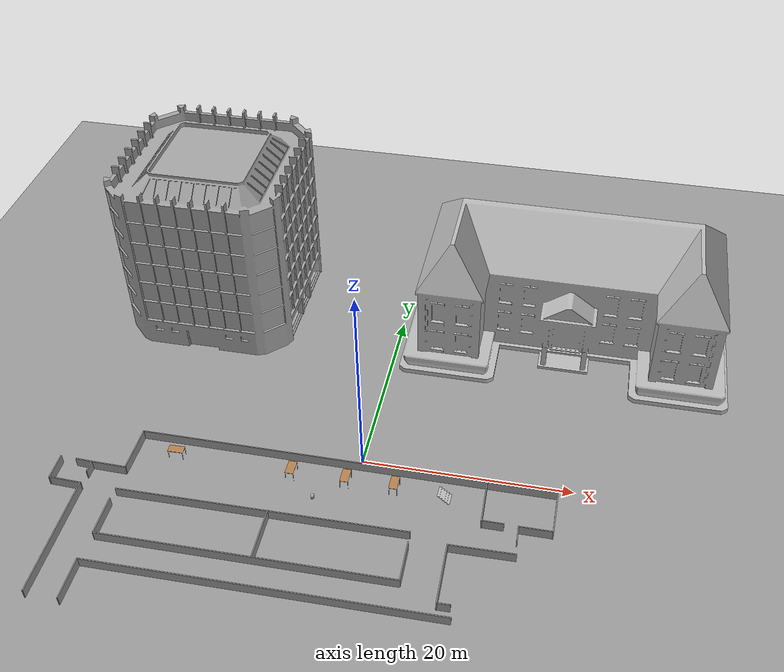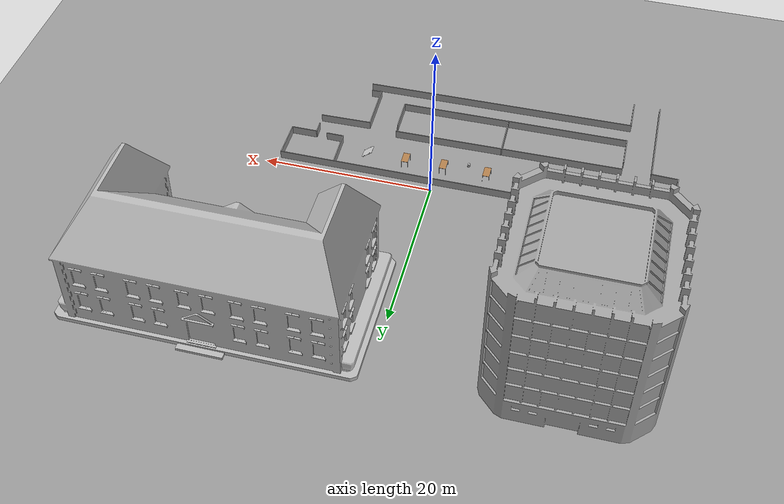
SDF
<sdf version="1.6">
 <world name="default">
  <light name="sun" type="directional">
   <pose>0 0 10 0 -0 0</pose>
   <diffuse>0.8 0.8 0.8 1</diffuse>
   <specular>0.2 0.2 0.2 1</specular>
   <attenuation>
    <range>1000</range>
    <constant>0.9</constant>
    <linear>0.01</linear>
    <quadratic>0.001</quadratic>
   </attenuation>
   <direction>0.5 0.1 -0.9</direction>
  </light>
  <scene><ambient>0.4 0.4 0.4 1</ambient><background>0.7 0.7 0.7 1</background><shadows>1</shadows></scene>
  <physics name="default_physics" default="0" type="ode">
   <max_step_size>0.01</max_step_size>
   <real_time_factor>1</real_time_factor>
   <real_time_update_rate>100</real_time_update_rate>
  </physics>
  <model name="ground_plane_0">
   <static>1</static>
   <link name="link">
    <collision name="collision">
     <geometry><plane><normal>0 0 1</normal><size>100 100</size></plane></geometry>
     <surface><friction><ode><mu>100</mu><mu2>50</mu2></ode></friction></surface>
    </collision>
    <visual name="visual">
     <cast_shadows>0</cast_shadows>
     <geometry><plane><normal>0 0 1</normal><size>100 100</size></plane></geometry>
     <material>
      <script><uri>file://media/materials/scripts/gazebo.material</uri><name>Gazebo/Grey</name></script>
     </material>
    </visual>
    <velocity_decay><linear>0</linear><angular>0</angular></velocity_decay>
   </link>
   <pose>0.497681 0 0 0 -0 0</pose>
  </model>
  <gravity>0 0 -9.8</gravity>
  <magnetic_field>6e-06 2.3e-05 -4.2e-05</magnetic_field>
  <atmosphere type="adiabatic"/>
  <spherical_coordinates>
   <surface_model>EARTH_WGS84</surface_model>
   <latitude_deg>0</latitude_deg>
   <longitude_deg>0</longitude_deg>
   <elevation>0</elevation>
   <heading_deg>0</heading_deg>
  </spherical_coordinates>
  <model name="mobile_base">
   <link name="base_footprint">
    <inertial>
     <pose>-0.002635 -4.1e-05 0.129243 0 -0 0</pose>
     <mass>4.6973</mass>
     <inertia>
      <ixx>0.1365</ixx>
      <ixy>-2.51802e-05</ixy>
      <ixz>0.0108194</ixz>
      <iyy>0.132157</iyy>
      <iyz>4.89572e-05</iyz>
      <izz>0.0741648</izz>
     </inertia>
    </inertial>
    <collision name="base_footprint_fixed_joint_lump__base_collision">
     <pose>0 0 0.06969 0 -0 0</pose>
     <geometry><cylinder><length>0.10938</length><radius>0.178</radius></cylinder></geometry>
    </collision>
    <collision name="base_footprint_fixed_joint_lump__camera_link_collision_1">
     <pose>-0.087 -0.0015 0.2972 0 -0 0</pose>
     <geometry><box><size>0.073 0.276 0.072</size></box></geometry>
    </collision>
    <collision name="base_footprint_fixed_joint_lump__caster_back_link_collision_2">
     <pose>-0.135 0 0.0192 -1.5708 0 0</pose>
     <geometry><cylinder><length>0.0176</length><radius>0.017</radius></cylinder></geometry>
     <surface>
      <contact><ode><kp>1e+06</kp><kd>100</kd><max_vel>1</max_vel><min_depth>0.001</min_depth></ode></contact>
      <friction><ode><mu>0</mu><mu2>0</mu2></ode></friction>
     </surface>
    </collision>
    <collision name="base_footprint_fixed_joint_lump__caster_front_link_collision_3">
     <pose>0.115 0 0.0172 -1.5708 0 0</pose>
     <geometry><cylinder><length>0.0176</length><radius>0.017</radius></cylinder></geometry>
     <surface>
      <contact><ode><kp>1e+06</kp><kd>100</kd><max_vel>1</max_vel><min_depth>0.001</min_depth></ode></contact>
      <friction><ode><mu>0</mu><mu2>0</mu2></ode></friction>
     </surface>
    </collision>
    <collision name="base_footprint_fixed_joint_lump__mount_asus_xtion_pro_link_collision_4">
     <pose>-0.1024 0 0.2822 0 -0 0</pose>
     <geometry><box><size>0.033 0.276 0.012</size></box></geometry>
    </collision>
    <collision name="base_footprint_fixed_joint_lump__plate_bottom_link_collision_5">
     <pose>0 0 0.1408 0 -0 0</pose>
     <geometry><cylinder><length>0.006</length><radius>0.17</radius></cylinder></geometry>
    </collision>
    <collision name="base_footprint_fixed_joint_lump__plate_middle_link_collision_6">
     <pose>0 0 0.1976 0 -0 0</pose>
     <geometry><cylinder><length>0.006</length><radius>0.17</radius></cylinder></geometry>
    </collision>
    <collision name="base_footprint_fixed_joint_lump__plate_top_link_collision_7">
     <pose>0 0 0.4068 0 -0 0</pose>
     <geometry><cylinder><length>0.006</length><radius>0.17</radius></cylinder></geometry>
    </collision>
    <collision name="base_footprint_fixed_joint_lump__pole_bottom_0_link_collision_8">
     <pose>0.12 0.082 0.113 0 -0 0</pose>
     <geometry><cylinder><length>0.0492</length><radius>0.006</radius></cylinder></geometry>
    </collision>
    <collision name="base_footprint_fixed_joint_lump__pole_bottom_1_link_collision_9">
     <pose>0.055 0.12 0.113 0 -0 0</pose>
     <geometry><cylinder><length>0.0492</length><radius>0.006</radius></cylinder></geometry>
    </collision>
    <collision name="base_footprint_fixed_joint_lump__pole_bottom_2_link_collision_10">
     <pose>-0.055 0.12 0.113 0 -0 0</pose>
     <geometry><cylinder><length>0.0492</length><radius>0.006</radius></cylinder></geometry>
    </collision>
    <collision name="base_footprint_fixed_joint_lump__pole_bottom_3_link_collision_11">
     <pose>0.12 -0.082 0.113 0 -0 0</pose>
     <geometry><cylinder><length>0.0492</length><radius>0.006</radius></cylinder></geometry>
    </collision>
    <collision name="base_footprint_fixed_joint_lump__pole_bottom_4_link_collision_12">
     <pose>0.055 -0.12 0.113 0 -0 0</pose>
     <geometry><cylinder><length>0.0492</length><radius>0.006</radius></cylinder></geometry>
    </collision>
    <collision name="base_footprint_fixed_joint_lump__pole_bottom_5_link_collision_13">
     <pose>-0.055 -0.12 0.113 0 -0 0</pose>
     <geometry><cylinder><length>0.0492</length><radius>0.006</radius></cylinder></geometry>
    </collision>
    <collision name="base_footprint_fixed_joint_lump__pole_kinect_0_link_collision_14">
     <pose>-0.1024 0.098 0.2474 0 -0 0</pose>
     <geometry><cylinder><length>0.0936</length><radius>0.006</radius></cylinder></geometry>
    </collision>
    <collision name="base_footprint_fixed_joint_lump__pole_kinect_1_link_collision_15">
     <pose>-0.1024 -0.098 0.2474 0 -0 0</pose>
     <geometry><cylinder><length>0.0936</length><radius>0.006</radius></cylinder></geometry>
    </collision>
    <collision name="base_footprint_fixed_joint_lump__pole_middle_0_link_collision_16">
     <pose>0.0381 0.1505 0.1742 0 -0 0</pose>
     <geometry><cylinder><length>0.0608</length><radius>0.006</radius></cylinder></geometry>
    </collision>
    <collision name="base_footprint_fixed_joint_lump__pole_middle_1_link_collision_17">
     <pose>0.0381 -0.1505 0.1742 0 -0 0</pose>
     <geometry><cylinder><length>0.0608</length><radius>0.006</radius></cylinder></geometry>
    </collision>
    <collision name="base_footprint_fixed_joint_lump__pole_middle_2_link_collision_18">
     <pose>-0.0381 0.1505 0.1742 0 -0 0</pose>
     <geometry><cylinder><length>0.0608</length><radius>0.006</radius></cylinder></geometry>
    </collision>
    <collision name="base_footprint_fixed_joint_lump__pole_middle_3_link_collision_19">
     <pose>-0.0381 -0.1505 0.1742 0 -0 0</pose>
     <geometry><cylinder><length>0.0608</length><radius>0.006</radius></cylinder></geometry>
    </collision>
    <collision name="base_footprint_fixed_joint_lump__pole_top_0_link_collision_20">
     <pose>0.0381 0.1505 0.3022 0 -0 0</pose>
     <geometry><cylinder><length>0.2032</length><radius>0.006</radius></cylinder></geometry>
    </collision>
    <collision name="base_footprint_fixed_joint_lump__pole_top_1_link_collision_21">
     <pose>0.0381 -0.1505 0.3022 0 -0 0</pose>
     <geometry><cylinder><length>0.2032</length><radius>0.006</radius></cylinder></geometry>
    </collision>
    <collision name="base_footprint_fixed_joint_lump__pole_top_2_link_collision_22">
     <pose>-0.0381 0.1505 0.3022 0 -0 0</pose>
     <geometry><cylinder><length>0.2032</length><radius>0.006</radius></cylinder></geometry>
    </collision>
    <collision name="base_footprint_fixed_joint_lump__pole_top_3_link_collision_23">
     <pose>-0.0381 -0.1505 0.3022 0 -0 0</pose>
     <geometry><cylinder><length>0.2032</length><radius>0.006</radius></cylinder></geometry>
    </collision>
    <visual name="base_footprint_fixed_joint_lump__base_link_visual">
     <pose>0.001 0 0.06219 0 -0 0</pose>
     <geometry>
      <mesh><scale>1 1 1</scale><uri>/opt/ros/kinetic/share/kobuki_description/meshes/main_body.dae</uri></mesh>
     </geometry>
     <material><script><uri>__default__</uri><name>__default__</name></script></material>
    </visual>
    <visual name="base_footprint_fixed_joint_lump__camera_link_visual_1">
     <pose>-0.102 0.002 0.3012 0 -0 0</pose>
     <geometry>
      <mesh>
       <scale>1 1 1</scale>
       <uri>/opt/ros/kinetic/share/turtlebot_description/meshes/sensors/xtion_pro_camera.dae</uri>
      </mesh>
     </geometry>
     <material><script><uri>__default__</uri><name>__default__</name></script></material>
    </visual>
    <visual name="base_footprint_fixed_joint_lump__mount_asus_xtion_pro_link_visual_2">
     <pose>-0.1024 0 0.2822 -1.5708 0 0</pose>
     <geometry>
      <mesh>
       <scale>1 1 1</scale>
       <uri>/opt/ros/kinetic/share/turtlebot_description/meshes/sensors/xtion_pro_stack.dae</uri>
      </mesh>
     </geometry>
    </visual>
    <visual name="base_footprint_fixed_joint_lump__plate_bottom_link_visual_3">
     <pose>0.02364 0 0.1408 0 -0 0</pose>
     <geometry>
      <mesh>
       <scale>1 1 1</scale>
       <uri>/opt/ros/kinetic/share/turtlebot_description/meshes/stacks/hexagons/plate_bottom.dae</uri>
      </mesh>
     </geometry>
    </visual>
    <visual name="base_footprint_fixed_joint_lump__plate_middle_link_visual_4">
     <pose>-0.01364 0 0.1976 0 -0 0</pose>
     <geometry>
      <mesh>
       <scale>1 1 1</scale>
       <uri>/opt/ros/kinetic/share/turtlebot_description/meshes/stacks/hexagons/plate_middle.dae</uri>
      </mesh>
     </geometry>
    </visual>
    <visual name="base_footprint_fixed_joint_lump__plate_top_link_visual_5">
     <pose>-0.01364 0 0.4068 0 -0 0</pose>
     <geometry>
      <mesh>
       <scale>1 1 1</scale>
       <uri>/opt/ros/kinetic/share/turtlebot_description/meshes/stacks/hexagons/plate_top.dae</uri>
      </mesh>
     </geometry>
    </visual>
    <visual name="base_footprint_fixed_joint_lump__pole_bottom_0_link_visual_6">
     <pose>0.12 0.082 0.113 0 -0 0</pose>
     <geometry>
      <mesh>
       <scale>1 1 1</scale>
       <uri>/opt/ros/kinetic/share/turtlebot_description/meshes/stacks/hexagons/pole_bottom.dae</uri>
      </mesh>
     </geometry>
    </visual>
    <visual name="base_footprint_fixed_joint_lump__pole_bottom_1_link_visual_7">
     <pose>0.055 0.12 0.113 0 -0 0</pose>
     <geometry>
      <mesh>
       <scale>1 1 1</scale>
       <uri>/opt/ros/kinetic/share/turtlebot_description/meshes/stacks/hexagons/pole_bottom.dae</uri>
      </mesh>
     </geometry>
    </visual>
    <visual name="base_footprint_fixed_joint_lump__pole_bottom_2_link_visual_8">
     <pose>-0.055 0.12 0.113 0 -0 0</pose>
     <geometry>
      <mesh>
       <scale>1 1 1</scale>
       <uri>/opt/ros/kinetic/share/turtlebot_description/meshes/stacks/hexagons/pole_bottom.dae</uri>
      </mesh>
     </geometry>
    </visual>
    <visual name="base_footprint_fixed_joint_lump__pole_bottom_3_link_visual_9">
     <pose>0.12 -0.082 0.113 0 -0 0</pose>
     <geometry>
      <mesh>
       <scale>1 1 1</scale>
       <uri>/opt/ros/kinetic/share/turtlebot_description/meshes/stacks/hexagons/pole_bottom.dae</uri>
      </mesh>
     </geometry>
    </visual>
    <visual name="base_footprint_fixed_joint_lump__pole_bottom_4_link_visual_10">
     <pose>0.055 -0.12 0.113 0 -0 0</pose>
     <geometry>
      <mesh>
       <scale>1 1 1</scale>
       <uri>/opt/ros/kinetic/share/turtlebot_description/meshes/stacks/hexagons/pole_bottom.dae</uri>
      </mesh>
     </geometry>
    </visual>
    <visual name="base_footprint_fixed_joint_lump__pole_bottom_5_link_visual_11">
     <pose>-0.055 -0.12 0.113 0 -0 0</pose>
     <geometry>
      <mesh>
       <scale>1 1 1</scale>
       <uri>/opt/ros/kinetic/share/turtlebot_description/meshes/stacks/hexagons/pole_bottom.dae</uri>
      </mesh>
     </geometry>
    </visual>
    <visual name="base_footprint_fixed_joint_lump__pole_kinect_0_link_visual_12">
     <pose>-0.1024 0.098 0.2374 0 -0 0</pose>
     <geometry>
      <mesh>
       <scale>1 1 1</scale>
       <uri>/opt/ros/kinetic/share/turtlebot_description/meshes/sensors/sensor_pole.dae</uri>
      </mesh>
     </geometry>
    </visual>
    <visual name="base_footprint_fixed_joint_lump__pole_kinect_1_link_visual_13">
     <pose>-0.1024 -0.098 0.2374 0 -0 0</pose>
     <geometry>
      <mesh>
       <scale>1 1 1</scale>
       <uri>/opt/ros/kinetic/share/turtlebot_description/meshes/sensors/sensor_pole.dae</uri>
      </mesh>
     </geometry>
    </visual>
    <visual name="base_footprint_fixed_joint_lump__pole_middle_0_link_visual_14">
     <pose>0.0381 0.1505 0.1742 3.14159 -0 3.14159</pose>
     <geometry>
      <mesh>
       <scale>1 1 1</scale>
       <uri>/opt/ros/kinetic/share/turtlebot_description/meshes/stacks/hexagons/pole_middle.dae</uri>
      </mesh>
     </geometry>
    </visual>
    <visual name="base_footprint_fixed_joint_lump__pole_middle_1_link_visual_15">
     <pose>0.0381 -0.1505 0.1742 3.14159 -0 3.14159</pose>
     <geometry>
      <mesh>
       <scale>1 1 1</scale>
       <uri>/opt/ros/kinetic/share/turtlebot_description/meshes/stacks/hexagons/pole_middle.dae</uri>
      </mesh>
     </geometry>
    </visual>
    <visual name="base_footprint_fixed_joint_lump__pole_middle_2_link_visual_16">
     <pose>-0.0381 0.1505 0.1742 3.14159 -0 3.14159</pose>
     <geometry>
      <mesh>
       <scale>1 1 1</scale>
       <uri>/opt/ros/kinetic/share/turtlebot_description/meshes/stacks/hexagons/pole_middle.dae</uri>
      </mesh>
     </geometry>
    </visual>
    <visual name="base_footprint_fixed_joint_lump__pole_middle_3_link_visual_17">
     <pose>-0.0381 -0.1505 0.1742 3.14159 -0 3.14159</pose>
     <geometry>
      <mesh>
       <scale>1 1 1</scale>
       <uri>/opt/ros/kinetic/share/turtlebot_description/meshes/stacks/hexagons/pole_middle.dae</uri>
      </mesh>
     </geometry>
    </visual>
    <visual name="base_footprint_fixed_joint_lump__pole_top_0_link_visual_18">
     <pose>0.0381 0.1505 0.3022 0 -0 0</pose>
     <geometry>
      <mesh>
       <scale>1 1 1</scale>
       <uri>/opt/ros/kinetic/share/turtlebot_description/meshes/stacks/hexagons/pole_top.dae</uri>
      </mesh>
     </geometry>
    </visual>
    <visual name="base_footprint_fixed_joint_lump__pole_top_1_link_visual_19">
     <pose>0.0381 -0.1505 0.3022 0 -0 0</pose>
     <geometry>
      <mesh>
       <scale>1 1 1</scale>
       <uri>/opt/ros/kinetic/share/turtlebot_description/meshes/stacks/hexagons/pole_top.dae</uri>
      </mesh>
     </geometry>
    </visual>
    <visual name="base_footprint_fixed_joint_lump__pole_top_2_link_visual_20">
     <pose>-0.0381 0.1505 0.3022 0 -0 0</pose>
     <geometry>
      <mesh>
       <scale>1 1 1</scale>
       <uri>/opt/ros/kinetic/share/turtlebot_description/meshes/stacks/hexagons/pole_top.dae</uri>
      </mesh>
     </geometry>
    </visual>
    <visual name="base_footprint_fixed_joint_lump__pole_top_3_link_visual_21">
     <pose>-0.0381 -0.1505 0.3022 0 -0 0</pose>
     <geometry>
      <mesh>
       <scale>1 1 1</scale>
       <uri>/opt/ros/kinetic/share/turtlebot_description/meshes/stacks/hexagons/pole_top.dae</uri>
      </mesh>
     </geometry>
    </visual>
    <sensor name="bumpers" type="contact">
     <always_on>1</always_on>
     <update_rate>50</update_rate>
     <visualize>1</visualize>
     <contact>
      <collision>base_footprint_fixed_joint_lump__base_collision</collision>
      <topic>__default_topic__</topic>
     </contact>
     <pose>0 0 0.0102 0 -0 0</pose>
    </sensor>
    <sensor name="camera" type="depth">
     <always_on>1</always_on>
     <update_rate>20</update_rate>
     <camera name="__default__">
      <horizontal_fov>1.0472</horizontal_fov>
      <image><format>B8G8R8</format><width>640</width><height>480</height></image>
      <clip><near>0.05</near><far>8</far></clip>
     </camera>
     <plugin name="kinect_camera_controller" filename="libgazebo_ros_openni_kinect.so">
      <cameraName>camera</cameraName>
      <alwaysOn>true</alwaysOn>
      <updateRate>10</updateRate>
      <imageTopicName>rgb/image_raw</imageTopicName>
      <depthImageTopicName>depth/image_raw</depthImageTopicName>
      <pointCloudTopicName>depth/points</pointCloudTopicName>
      <cameraInfoTopicName>rgb/camera_info</cameraInfoTopicName>
      <depthImageCameraInfoTopicName>depth/camera_info</depthImageCameraInfoTopicName>
      <frameName>camera_depth_optical_frame</frameName>
      <baseline>0.1</baseline>
      <distortion_k1>0.0</distortion_k1>
      <distortion_k2>0.0</distortion_k2>
      <distortion_k3>0.0</distortion_k3>
      <distortion_t1>0.0</distortion_t1>
      <distortion_t2>0.0</distortion_t2>
      <pointCloudCutoff>0.4</pointCloudCutoff>
      <robotNamespace>/</robotNamespace>
     </plugin>
     <pose>-0.087 -0.0015 0.2972 0 -0 0</pose>
    </sensor>
    <sensor name="cliff_sensor_front" type="ray">
     <always_on>1</always_on>
     <update_rate>50</update_rate>
     <visualize>1</visualize>
     <ray>
      <scan>
       <horizontal>
        <samples>50</samples>
        <resolution>1</resolution>
        <min_angle>-0.0436</min_angle>
        <max_angle>0.0436</max_angle>
       </horizontal>
       <vertical><samples>1</samples><min_angle>0</min_angle><max_angle>0</max_angle></vertical>
      </scan>
      <range><min>0.01</min><max>0.15</max><resolution>1</resolution></range>
     </ray>
     <pose>0.156 0 0.0316 3.14159 1.57079 3.14159</pose>
    </sensor>
    <sensor name="cliff_sensor_left" type="ray">
     <always_on>1</always_on>
     <update_rate>50</update_rate>
     <visualize>1</visualize>
     <ray>
      <scan>
       <horizontal>
        <samples>50</samples>
        <resolution>1</resolution>
        <min_angle>-0.0436</min_angle>
        <max_angle>0.0436</max_angle>
       </horizontal>
       <vertical><samples>1</samples><min_angle>0</min_angle><max_angle>0</max_angle></vertical>
      </scan>
      <range><min>0.01</min><max>0.15</max><resolution>1</resolution></range>
     </ray>
     <pose>0.08734 0.13601 0.0316 3.14159 1.57079 3.14159</pose>
    </sensor>
    <sensor name="cliff_sensor_right" type="ray">
     <always_on>1</always_on>
     <update_rate>50</update_rate>
     <visualize>1</visualize>
     <ray>
      <scan>
       <horizontal>
        <samples>50</samples>
        <resolution>1</resolution>
        <min_angle>-0.0436</min_angle>
        <max_angle>0.0436</max_angle>
       </horizontal>
       <vertical><samples>1</samples><min_angle>0</min_angle><max_angle>0</max_angle></vertical>
      </scan>
      <range><min>0.01</min><max>0.15</max><resolution>1</resolution></range>
     </ray>
     <pose>0.085 -0.13601 0.0316 3.14159 1.57079 3.14159</pose>
    </sensor>
    <sensor name="imu" type="imu">
     <always_on>1</always_on>
     <update_rate>50</update_rate>
     <visualize>0</visualize>
     <imu>
      <angular_velocity>
       <x>
        <noise type="gaussian">
         <mean>0</mean>
         <stddev>1.96e-06</stddev>
         <bias_mean>0</bias_mean>
         <bias_stddev>0</bias_stddev>
        </noise>
       </x>
       <y>
        <noise type="gaussian">
         <mean>0</mean>
         <stddev>1.96e-06</stddev>
         <bias_mean>0</bias_mean>
         <bias_stddev>0</bias_stddev>
        </noise>
       </y>
       <z>
        <noise type="gaussian">
         <mean>0</mean>
         <stddev>1.96e-06</stddev>
         <bias_mean>0</bias_mean>
         <bias_stddev>0</bias_stddev>
        </noise>
       </z>
      </angular_velocity>
      <linear_acceleration>
       <x>
        <noise type="gaussian">
         <mean>0</mean>
         <stddev>0.017</stddev>
         <bias_mean>0.1</bias_mean>
         <bias_stddev>0.001</bias_stddev>
        </noise>
       </x>
       <y>
        <noise type="gaussian">
         <mean>0</mean>
         <stddev>0.017</stddev>
         <bias_mean>0.1</bias_mean>
         <bias_stddev>0.001</bias_stddev>
        </noise>
       </y>
       <z>
        <noise type="gaussian">
         <mean>0</mean>
         <stddev>0.017</stddev>
         <bias_mean>0.1</bias_mean>
         <bias_stddev>0.001</bias_stddev>
        </noise>
       </z>
      </linear_acceleration>
     </imu>
     <pose>0.056 0.062 0.0304 0 -0 0</pose>
    </sensor>
   </link>
   <link name="wheel_left_link">
    <pose>0 0.115 0.0352 -1.5708 0 0</pose>
    <inertial>
     <mass>0.01</mass>
     <inertia><ixx>0.001</ixx><ixy>0</ixy><ixz>0</ixz><iyy>0.001</iyy><iyz>0</iyz><izz>0.001</izz></inertia>
    </inertial>
    <collision name="wheel_left_link_collision">
     <geometry><cylinder><length>0.0206</length><radius>0.0352</radius></cylinder></geometry>
     <surface>
      <contact><ode><kp>1e+06</kp><kd>100</kd><max_vel>1</max_vel><min_depth>0.001</min_depth></ode></contact>
      <friction><ode><mu>1</mu><mu2>1</mu2></ode></friction>
     </surface>
    </collision>
    <visual name="wheel_left_link_visual">
     <geometry>
      <mesh><scale>1 1 1</scale><uri>/opt/ros/kinetic/share/kobuki_description/meshes/wheel.dae</uri></mesh>
     </geometry>
     <material><script><uri>__default__</uri><name>__default__</name></script></material>
    </visual>
   </link>
   <joint name="wheel_left_joint" type="revolute">
    <child>wheel_left_link</child>
    <parent>base_footprint</parent>
    <axis>
     <xyz>0 1 0</xyz>
     <limit><lower>-1e+16</lower><upper>1e+16</upper></limit>
     <dynamics><spring_reference>0</spring_reference><spring_stiffness>0</spring_stiffness></dynamics>
     <use_parent_model_frame>1</use_parent_model_frame>
    </axis>
   </joint>
   <link name="wheel_right_link">
    <pose>0 -0.115 0.0352 -1.5708 0 0</pose>
    <inertial>
     <mass>0.01</mass>
     <inertia><ixx>0.001</ixx><ixy>0</ixy><ixz>0</ixz><iyy>0.001</iyy><iyz>0</iyz><izz>0.001</izz></inertia>
    </inertial>
    <collision name="wheel_right_link_collision">
     <geometry><cylinder><length>0.0206</length><radius>0.035</radius></cylinder></geometry>
     <surface>
      <contact><ode><kp>1e+06</kp><kd>100</kd><max_vel>1</max_vel><min_depth>0.001</min_depth></ode></contact>
      <friction><ode><mu>1</mu><mu2>1</mu2></ode></friction>
     </surface>
    </collision>
    <visual name="wheel_right_link_visual">
     <geometry>
      <mesh><scale>1 1 1</scale><uri>/opt/ros/kinetic/share/kobuki_description/meshes/wheel.dae</uri></mesh>
     </geometry>
     <material><script><uri>__default__</uri><name>__default__</name></script></material>
    </visual>
   </link>
   <joint name="wheel_right_joint" type="revolute">
    <child>wheel_right_link</child>
    <parent>base_footprint</parent>
    <axis>
     <xyz>0 1 0</xyz>
     <limit><lower>-1e+16</lower><upper>1e+16</upper></limit>
     <dynamics><spring_reference>0</spring_reference><spring_stiffness>0</spring_stiffness></dynamics>
     <use_parent_model_frame>1</use_parent_model_frame>
    </axis>
   </joint>
   <static>0</static>
   <plugin name="kobuki_controller" filename="libgazebo_ros_kobuki.so">
    <publish_tf>1</publish_tf>
    <left_wheel_joint_name>wheel_left_joint</left_wheel_joint_name>
    <right_wheel_joint_name>wheel_right_joint</right_wheel_joint_name>
    <wheel_separation>.230</wheel_separation>
    <wheel_diameter>0.070</wheel_diameter>
    <torque>1.0</torque>
    <velocity_command_timeout>0.6</velocity_command_timeout>
    <cliff_sensor_left_name>cliff_sensor_left</cliff_sensor_left_name>
    <cliff_sensor_center_name>cliff_sensor_front</cliff_sensor_center_name>
    <cliff_sensor_right_name>cliff_sensor_right</cliff_sensor_right_name>
    <cliff_detection_threshold>0.04</cliff_detection_threshold>
    <bumper_name>bumpers</bumper_name>
    <imu_name>imu</imu_name>
    <robotNamespace>/</robotNamespace>
   </plugin>
   <pose>-3.52655 -5.10992 -0.001131 5.8e-05 -0.007995 -1.50782</pose>
  </model>
  <model name="big_project_room">
   <link name="link">
    <pose>14.0349 -2.99213 2.5e-05 0 -0 0.019261</pose>
    <inertial>
     <mass>0.0501598</mass>
     <inertia>
      <ixx>0.00418042</ixx>
      <ixy>0</ixy>
      <ixz>0</ixz>
      <iyy>0.104263</iyy>
      <iyz>0</iyz>
      <izz>0.100083</izz>
     </inertia>
    </inertial>
    <visual name="visual">
     <geometry><box><size>6.096 0.10251 1</size></box></geometry>
     <material>
      <script><name>Gazebo/Grey</name><uri>file://media/materials/scripts/gazebo.material</uri></script>
      <shader type="pixel"><normal_map>__default__</normal_map></shader>
      <ambient>1 1 1 1</ambient>
      <diffuse>0.7 0.7 0.7 1</diffuse>
      <specular>0.01 0.01 0.01 1</specular>
      <emissive>0 0 0 1</emissive>
     </material>
    </visual>
    <collision name="collision">
     <geometry><box><size>6.096 0.10251 1</size></box></geometry>
     <surface>
      <friction>
       <ode><mu>1</mu><mu2>1</mu2><fdir1>0 0 0</fdir1><slip1>0</slip1><slip2>0</slip2></ode>
       <torsional>
        <coefficient>1</coefficient>
        <patch_radius>0</patch_radius>
        <surface_radius>0</surface_radius>
        <use_patch_radius>1</use_patch_radius>
        <ode><slip>0</slip></ode>
       </torsional>
      </friction>
      <bounce><restitution_coefficient>0</restitution_coefficient><threshold>1e+06</threshold></bounce>
      <contact>
       <collide_without_contact>0</collide_without_contact>
       <collide_without_contact_bitmask>1</collide_without_contact_bitmask>
       <collide_bitmask>1</collide_bitmask>
       <ode>
        <soft_cfm>0</soft_cfm>
        <soft_erp>0.2</soft_erp>
        <kp>1e+13</kp>
        <kd>1</kd>
        <max_vel>0.01</max_vel>
        <min_depth>0</min_depth>
       </ode>
       <bullet>
        <split_impulse>1</split_impulse>
        <split_impulse_penetration_threshold>-0.01</split_impulse_penetration_threshold>
        <soft_cfm>0</soft_cfm>
        <soft_erp>0.2</soft_erp>
        <kp>1e+13</kp>
        <kd>1</kd>
       </bullet>
      </contact>
     </surface>
    </collision>
   </link>
   <link name="link_0_clone">
    <pose>19.9441 2.29599 -0.01875 0.00066 0.00066 -1.57077</pose>
    <inertial>
     <mass>1</mass>
     <inertia>
      <ixx>0.166667</ixx>
      <ixy>0</ixy>
      <ixz>0</ixz>
      <iyy>0.166667</iyy>
      <iyz>0</iyz>
      <izz>0.166667</izz>
     </inertia>
    </inertial>
    <visual name="visual">
     <geometry><box><size>4.527 0.1 1</size></box></geometry>
     <material>
      <lighting>1</lighting>
      <script><uri>file://media/materials/scripts/gazebo.material</uri><name>Gazebo/Grey</name></script>
      <shader type="pixel"><normal_map>__default__</normal_map></shader>
      <ambient>1 1 1 1</ambient>
      <diffuse>0.7 0.7 0.7 1</diffuse>
      <specular>0.01 0.01 0.01 1</specular>
      <emissive>0 0 0 1</emissive>
     </material>
    </visual>
    <collision name="collision">
     <geometry><box><size>4.572 0.1 1</size></box></geometry>
     <surface>
      <friction>
       <ode><mu>1</mu><mu2>1</mu2><fdir1>0 0 0</fdir1><slip1>0</slip1><slip2>0</slip2></ode>
       <torsional>
        <coefficient>1</coefficient>
        <patch_radius>0</patch_radius>
        <surface_radius>0</surface_radius>
        <use_patch_radius>1</use_patch_radius>
        <ode><slip>0</slip></ode>
       </torsional>
      </friction>
      <bounce><restitution_coefficient>0</restitution_coefficient><threshold>1e+06</threshold></bounce>
      <contact>
       <collide_without_contact>0</collide_without_contact>
       <collide_without_contact_bitmask>1</collide_without_contact_bitmask>
       <collide_bitmask>1</collide_bitmask>
       <ode>
        <soft_cfm>0</soft_cfm>
        <soft_erp>0.2</soft_erp>
        <kp>1e+13</kp>
        <kd>1</kd>
        <max_vel>0.01</max_vel>
        <min_depth>0</min_depth>
       </ode>
       <bullet>
        <split_impulse>1</split_impulse>
        <split_impulse_penetration_threshold>-0.01</split_impulse_penetration_threshold>
        <soft_cfm>0</soft_cfm>
        <soft_erp>0.2</soft_erp>
        <kp>1e+13</kp>
        <kd>1</kd>
       </bullet>
      </contact>
     </surface>
    </collision>
   </link>
   <link name="link_0_clone_clone">
    <pose>-19.9604 2.29143 -0.013844 0.00066 0 -1.57081</pose>
    <inertial>
     <mass>1</mass>
     <inertia>
      <ixx>0.166667</ixx>
      <ixy>0</ixy>
      <ixz>0</ixz>
      <iyy>0.166667</iyy>
      <iyz>0</iyz>
      <izz>0.166667</izz>
     </inertia>
    </inertial>
    <visual name="visual">
     <geometry><box><size>4.527 0.1 1</size></box></geometry>
     <material>
      <lighting>1</lighting>
      <script><uri>file://media/materials/scripts/gazebo.material</uri><name>Gazebo/Grey</name></script>
      <shader type="pixel"><normal_map>__default__</normal_map></shader>
      <ambient>1 1 1 1</ambient>
      <diffuse>0.7 0.7 0.7 1</diffuse>
      <specular>0.01 0.01 0.01 1</specular>
      <emissive>0 0 0 1</emissive>
     </material>
    </visual>
    <collision name="collision">
     <geometry><box><size>4.572 0.1 1</size></box></geometry>
     <surface>
      <friction>
       <ode><mu>1</mu><mu2>1</mu2><fdir1>0 0 0</fdir1><slip1>0</slip1><slip2>0</slip2></ode>
       <torsional>
        <coefficient>1</coefficient>
        <patch_radius>0</patch_radius>
        <surface_radius>0</surface_radius>
        <use_patch_radius>1</use_patch_radius>
        <ode><slip>0</slip></ode>
       </torsional>
      </friction>
      <bounce><restitution_coefficient>0</restitution_coefficient><threshold>1e+06</threshold></bounce>
      <contact>
       <collide_without_contact>0</collide_without_contact>
       <collide_without_contact_bitmask>1</collide_without_contact_bitmask>
       <collide_bitmask>1</collide_bitmask>
       <ode>
        <soft_cfm>0</soft_cfm>
        <soft_erp>0.2</soft_erp>
        <kp>1e+13</kp>
        <kd>1</kd>
        <max_vel>0.01</max_vel>
        <min_depth>0</min_depth>
       </ode>
       <bullet>
        <split_impulse>1</split_impulse>
        <split_impulse_penetration_threshold>-0.01</split_impulse_penetration_threshold>
        <soft_cfm>0</soft_cfm>
        <soft_erp>0.2</soft_erp>
        <kp>1e+13</kp>
        <kd>1</kd>
       </bullet>
      </contact>
     </surface>
    </collision>
   </link>
   <link name="link_0_clone_clone_clone_0">
    <pose>14.5732 0.114647 0.004935 -0.000664 0.000656 3.13495</pose>
    <inertial>
     <mass>1</mass>
     <inertia>
      <ixx>0.166667</ixx>
      <ixy>0</ixy>
      <ixz>0</ixz>
      <iyy>0.166667</iyy>
      <iyz>0</iyz>
      <izz>0.166667</izz>
     </inertia>
    </inertial>
    <visual name="visual">
     <geometry><box><size>2 0.1 1</size></box></geometry>
     <material>
      <lighting>1</lighting>
      <script><uri>file://media/materials/scripts/gazebo.material</uri><name>Gazebo/Grey</name></script>
      <shader type="pixel"><normal_map>__default__</normal_map></shader>
      <ambient>1 1 1 1</ambient>
      <diffuse>0.7 0.7 0.7 1</diffuse>
      <specular>0.01 0.01 0.01 1</specular>
      <emissive>0 0 0 1</emissive>
     </material>
    </visual>
    <collision name="collision">
     <geometry><box><size>2 0.1 1</size></box></geometry>
     <surface>
      <friction>
       <ode><mu>1</mu><mu2>1</mu2><fdir1>0 0 0</fdir1><slip1>0</slip1><slip2>0</slip2></ode>
       <torsional>
        <coefficient>1</coefficient>
        <patch_radius>0</patch_radius>
        <surface_radius>0</surface_radius>
        <use_patch_radius>1</use_patch_radius>
        <ode><slip>0</slip></ode>
       </torsional>
      </friction>
      <bounce><restitution_coefficient>0</restitution_coefficient><threshold>1e+06</threshold></bounce>
      <contact>
       <collide_without_contact>0</collide_without_contact>
       <collide_without_contact_bitmask>1</collide_without_contact_bitmask>
       <collide_bitmask>1</collide_bitmask>
       <ode>
        <soft_cfm>0</soft_cfm>
        <soft_erp>0.2</soft_erp>
        <kp>1e+13</kp>
        <kd>1</kd>
        <max_vel>0.01</max_vel>
        <min_depth>0</min_depth>
       </ode>
       <bullet>
        <split_impulse>1</split_impulse>
        <split_impulse_penetration_threshold>-0.01</split_impulse_penetration_threshold>
        <soft_cfm>0</soft_cfm>
        <soft_erp>0.2</soft_erp>
        <kp>1e+13</kp>
        <kd>1</kd>
       </bullet>
      </contact>
     </surface>
    </collision>
   </link>
   <link name="link_0_clone_clone_clone_clone_0">
    <pose>16.8828 -0.632141 0.009219 -0.000709 -0.001294 1.60824</pose>
    <inertial>
     <mass>1</mass>
     <inertia>
      <ixx>0.166667</ixx>
      <ixy>0</ixy>
      <ixz>0</ixz>
      <iyy>0.166667</iyy>
      <iyz>0</iyz>
      <izz>0.166667</izz>
     </inertia>
    </inertial>
    <visual name="visual">
     <geometry><box><size>1.524 0.1 1</size></box></geometry>
     <material>
      <lighting>1</lighting>
      <script><uri>file://media/materials/scripts/gazebo.material</uri><name>Gazebo/Grey</name></script>
      <shader type="pixel"><normal_map>__default__</normal_map></shader>
      <ambient>1 1 1 1</ambient>
      <diffuse>0.7 0.7 0.7 1</diffuse>
      <specular>0.01 0.01 0.01 1</specular>
      <emissive>0 0 0 1</emissive>
     </material>
    </visual>
    <collision name="collision">
     <geometry><box><size>1.524 0.1 1</size></box></geometry>
     <surface>
      <friction>
       <ode><mu>1</mu><mu2>1</mu2><fdir1>0 0 0</fdir1><slip1>0</slip1><slip2>0</slip2></ode>
       <torsional>
        <coefficient>1</coefficient>
        <patch_radius>0</patch_radius>
        <surface_radius>0</surface_radius>
        <use_patch_radius>1</use_patch_radius>
        <ode><slip>0</slip></ode>
       </torsional>
      </friction>
      <bounce><restitution_coefficient>0</restitution_coefficient><threshold>1e+06</threshold></bounce>
      <contact>
       <collide_without_contact>0</collide_without_contact>
       <collide_without_contact_bitmask>1</collide_without_contact_bitmask>
       <collide_bitmask>1</collide_bitmask>
       <ode>
        <soft_cfm>0</soft_cfm>
        <soft_erp>0.2</soft_erp>
        <kp>1e+13</kp>
        <kd>1</kd>
        <max_vel>0.01</max_vel>
        <min_depth>0</min_depth>
       </ode>
       <bullet>
        <split_impulse>1</split_impulse>
        <split_impulse_penetration_threshold>-0.01</split_impulse_penetration_threshold>
        <soft_cfm>0</soft_cfm>
        <soft_erp>0.2</soft_erp>
        <kp>1e+13</kp>
        <kd>1</kd>
       </bullet>
      </contact>
     </surface>
    </collision>
   </link>
   <link name="link_0_clone_clone_clone_clone_1">
    <pose>18.3965 0.082315 0.010039 -0.001319 0.000662 -3.14011</pose>
    <inertial>
     <mass>1</mass>
     <inertia>
      <ixx>0.166667</ixx>
      <ixy>0</ixy>
      <ixz>0</ixz>
      <iyy>0.166667</iyy>
      <iyz>0</iyz>
      <izz>0.166667</izz>
     </inertia>
    </inertial>
    <visual name="visual">
     <geometry><box><size>3 0.1 1</size></box></geometry>
     <material>
      <lighting>1</lighting>
      <script><uri>file://media/materials/scripts/gazebo.material</uri><name>Gazebo/Grey</name></script>
      <shader type="pixel"><normal_map>__default__</normal_map></shader>
      <ambient>1 1 1 1</ambient>
      <diffuse>0.7 0.7 0.7 1</diffuse>
      <specular>0.01 0.01 0.01 1</specular>
      <emissive>0 0 0 1</emissive>
     </material>
    </visual>
    <collision name="collision">
     <geometry><box><size>3 0.1 1</size></box></geometry>
     <surface>
      <friction>
       <ode><mu>1</mu><mu2>1</mu2><fdir1>0 0 0</fdir1><slip1>0</slip1><slip2>0</slip2></ode>
       <torsional>
        <coefficient>1</coefficient>
        <patch_radius>0</patch_radius>
        <surface_radius>0</surface_radius>
        <use_patch_radius>1</use_patch_radius>
        <ode><slip>0</slip></ode>
       </torsional>
      </friction>
      <bounce><restitution_coefficient>0</restitution_coefficient><threshold>1e+06</threshold></bounce>
      <contact>
       <collide_without_contact>0</collide_without_contact>
       <collide_without_contact_bitmask>1</collide_without_contact_bitmask>
       <collide_bitmask>1</collide_bitmask>
       <ode>
        <soft_cfm>0</soft_cfm>
        <soft_erp>0.2</soft_erp>
        <kp>1e+13</kp>
        <kd>1</kd>
        <max_vel>0.01</max_vel>
        <min_depth>0</min_depth>
       </ode>
       <bullet>
        <split_impulse>1</split_impulse>
        <split_impulse_penetration_threshold>-0.01</split_impulse_penetration_threshold>
        <soft_cfm>0</soft_cfm>
        <soft_erp>0.2</soft_erp>
        <kp>1e+13</kp>
        <kd>1</kd>
       </bullet>
      </contact>
     </surface>
    </collision>
   </link>
   <link name="link_clone">
    <pose>-0.007377 4.60801 0.003041 0.00066 -0 0</pose>
    <inertial>
     <mass>0.0501598</mass>
     <inertia>
      <ixx>0.00418042</ixx>
      <ixy>0</ixy>
      <ixz>0</ixz>
      <iyy>0.104263</iyy>
      <iyz>0</iyz>
      <izz>0.100083</izz>
     </inertia>
    </inertial>
    <visual name="visual">
     <geometry><box><size>40 0.10251 1</size></box></geometry>
     <material>
      <script><name>Gazebo/Grey</name><uri>file://media/materials/scripts/gazebo.material</uri></script>
      <shader type="pixel"><normal_map>__default__</normal_map></shader>
      <ambient>1 1 1 1</ambient>
      <diffuse>0.7 0.7 0.7 1</diffuse>
      <specular>0.01 0.01 0.01 1</specular>
      <emissive>0 0 0 1</emissive>
     </material>
    </visual>
    <collision name="collision">
     <geometry><box><size>40 0.10251 1</size></box></geometry>
     <surface>
      <friction>
       <ode><mu>1</mu><mu2>1</mu2><fdir1>0 0 0</fdir1><slip1>0</slip1><slip2>0</slip2></ode>
       <torsional>
        <coefficient>1</coefficient>
        <patch_radius>0</patch_radius>
        <surface_radius>0</surface_radius>
        <use_patch_radius>1</use_patch_radius>
        <ode><slip>0</slip></ode>
       </torsional>
      </friction>
      <bounce><restitution_coefficient>0</restitution_coefficient><threshold>1e+06</threshold></bounce>
      <contact>
       <collide_without_contact>0</collide_without_contact>
       <collide_without_contact_bitmask>1</collide_without_contact_bitmask>
       <collide_bitmask>1</collide_bitmask>
       <ode>
        <soft_cfm>0</soft_cfm>
        <soft_erp>0.2</soft_erp>
        <kp>1e+13</kp>
        <kd>1</kd>
        <max_vel>0.01</max_vel>
        <min_depth>0</min_depth>
       </ode>
       <bullet>
        <split_impulse>1</split_impulse>
        <split_impulse_penetration_threshold>-0.01</split_impulse_penetration_threshold>
        <soft_cfm>0</soft_cfm>
        <soft_erp>0.2</soft_erp>
        <kp>1e+13</kp>
        <kd>1</kd>
       </bullet>
      </contact>
     </surface>
    </collision>
   </link>
   <link name="link_clone_0">
    <pose>13.4826 2.33415 0.001565 1.7e-05 0.00066 -1.54442</pose>
    <inertial>
     <mass>0.0373227</mass>
     <inertia>
      <ixx>0.00314291</ixx>
      <ixy>0</ixy>
      <ixz>0</ixz>
      <iyy>0.067101</iyy>
      <iyz>0</iyz>
      <izz>0.0640235</izz>
     </inertia>
    </inertial>
    <visual name="visual">
     <geometry><box><size>4.53589 0.10251 1</size></box></geometry>
     <material>
      <script><name>Gazebo/Grey</name><uri>file://media/materials/scripts/gazebo.material</uri></script>
      <shader type="pixel"><normal_map>__default__</normal_map></shader>
      <ambient>1 1 1 1</ambient>
      <diffuse>0.7 0.7 0.7 1</diffuse>
      <specular>0.01 0.01 0.01 1</specular>
      <emissive>0 0 0 1</emissive>
     </material>
    </visual>
    <collision name="collision">
     <geometry><box><size>4.53589 0.10251 1</size></box></geometry>
     <surface>
      <friction>
       <ode><mu>1</mu><mu2>1</mu2><fdir1>0 0 0</fdir1><slip1>0</slip1><slip2>0</slip2></ode>
       <torsional>
        <coefficient>1</coefficient>
        <patch_radius>0</patch_radius>
        <surface_radius>0</surface_radius>
        <use_patch_radius>1</use_patch_radius>
        <ode><slip>0</slip></ode>
       </torsional>
      </friction>
      <bounce><restitution_coefficient>0</restitution_coefficient><threshold>1e+06</threshold></bounce>
      <contact>
       <collide_without_contact>0</collide_without_contact>
       <collide_without_contact_bitmask>1</collide_without_contact_bitmask>
       <collide_bitmask>1</collide_bitmask>
       <ode>
        <soft_cfm>0</soft_cfm>
        <soft_erp>0.2</soft_erp>
        <kp>1e+13</kp>
        <kd>1</kd>
        <max_vel>0.01</max_vel>
        <min_depth>0</min_depth>
       </ode>
       <bullet>
        <split_impulse>1</split_impulse>
        <split_impulse_penetration_threshold>-0.01</split_impulse_penetration_threshold>
        <soft_cfm>0</soft_cfm>
        <soft_erp>0.2</soft_erp>
        <kp>1e+13</kp>
        <kd>1</kd>
       </bullet>
      </contact>
     </surface>
    </collision>
   </link>
   <link name="link_clone_1">
    <pose>11.064 -6.05479 -0.003971 1.2e-05 0.00066 -1.55284</pose>
    <inertial>
     <mass>0.0501598</mass>
     <inertia>
      <ixx>0.00418042</ixx>
      <ixy>0</ixy>
      <ixz>0</ixz>
      <iyy>0.104263</iyy>
      <iyz>0</iyz>
      <izz>0.100083</izz>
     </inertia>
    </inertial>
    <visual name="visual">
     <geometry><box><size>6.096 0.10251 1</size></box></geometry>
     <material>
      <script><name>Gazebo/Grey</name><uri>file://media/materials/scripts/gazebo.material</uri></script>
      <shader type="pixel"><normal_map>__default__</normal_map></shader>
      <ambient>1 1 1 1</ambient>
      <diffuse>0.7 0.7 0.7 1</diffuse>
      <specular>0.01 0.01 0.01 1</specular>
      <emissive>0 0 0 1</emissive>
     </material>
    </visual>
    <collision name="collision">
     <geometry><box><size>6.096 0.10251 1</size></box></geometry>
     <surface>
      <friction>
       <ode><mu>1</mu><mu2>1</mu2><fdir1>0 0 0</fdir1><slip1>0</slip1><slip2>0</slip2></ode>
       <torsional>
        <coefficient>1</coefficient>
        <patch_radius>0</patch_radius>
        <surface_radius>0</surface_radius>
        <use_patch_radius>1</use_patch_radius>
        <ode><slip>0</slip></ode>
       </torsional>
      </friction>
      <bounce><restitution_coefficient>0</restitution_coefficient><threshold>1e+06</threshold></bounce>
      <contact>
       <collide_without_contact>0</collide_without_contact>
       <collide_without_contact_bitmask>1</collide_without_contact_bitmask>
       <collide_bitmask>1</collide_bitmask>
       <ode>
        <soft_cfm>0</soft_cfm>
        <soft_erp>0.2</soft_erp>
        <kp>1e+13</kp>
        <kd>1</kd>
        <max_vel>0.01</max_vel>
        <min_depth>0</min_depth>
       </ode>
       <bullet>
        <split_impulse>1</split_impulse>
        <split_impulse_penetration_threshold>-0.01</split_impulse_penetration_threshold>
        <soft_cfm>0</soft_cfm>
        <soft_erp>0.2</soft_erp>
        <kp>1e+13</kp>
        <kd>1</kd>
       </bullet>
      </contact>
     </surface>
    </collision>
   </link>
   <link name="link_clone_1_clone">
    <pose>-3.72157 -10.3844 -0.010858 -0.00132 1.3e-05 -3.13177</pose>
    <inertial>
     <mass>0.268169</mass>
     <inertia>
      <ixx>0.0225823</ixx>
      <ixy>0</ixy>
      <ixz>0</ixz>
      <iyy>23.7593</iyy>
      <iyz>0</iyz>
      <izz>23.7372</izz>
     </inertia>
    </inertial>
    <visual name="visual">
     <geometry><box><size>32.5911 0.10251 1</size></box></geometry>
     <material>
      <script><name>Gazebo/Grey</name><uri>file://media/materials/scripts/gazebo.material</uri></script>
      <shader type="pixel"><normal_map>__default__</normal_map></shader>
      <ambient>1 1 1 1</ambient>
      <diffuse>0.7 0.7 0.7 1</diffuse>
      <specular>0.01 0.01 0.01 1</specular>
      <emissive>0 0 0 1</emissive>
     </material>
    </visual>
    <collision name="collision">
     <geometry><box><size>32.5911 0.10251 1</size></box></geometry>
     <surface>
      <friction>
       <ode><mu>1</mu><mu2>1</mu2><fdir1>0 0 0</fdir1><slip1>0</slip1><slip2>0</slip2></ode>
       <torsional>
        <coefficient>1</coefficient>
        <patch_radius>0</patch_radius>
        <surface_radius>0</surface_radius>
        <use_patch_radius>1</use_patch_radius>
        <ode><slip>0</slip></ode>
       </torsional>
      </friction>
      <bounce><restitution_coefficient>0</restitution_coefficient><threshold>1e+06</threshold></bounce>
      <contact>
       <collide_without_contact>0</collide_without_contact>
       <collide_without_contact_bitmask>1</collide_without_contact_bitmask>
       <collide_bitmask>1</collide_bitmask>
       <ode>
        <soft_cfm>0</soft_cfm>
        <soft_erp>0.2</soft_erp>
        <kp>1e+13</kp>
        <kd>1</kd>
        <max_vel>0.01</max_vel>
        <min_depth>0</min_depth>
       </ode>
       <bullet>
        <split_impulse>1</split_impulse>
        <split_impulse_penetration_threshold>-0.01</split_impulse_penetration_threshold>
        <soft_cfm>0</soft_cfm>
        <soft_erp>0.2</soft_erp>
        <kp>1e+13</kp>
        <kd>1</kd>
       </bullet>
      </contact>
     </surface>
    </collision>
   </link>
   <link name="link_clone_1_clone_0">
    <pose>11.726 -9.03721 -0.009925 -0.00132 2.9e-05 -3.11953</pose>
    <inertial>
     <mass>0.00975708</mass>
     <inertia>
      <ixx>0.000821634</ixx>
      <ixy>0</ixy>
      <ixz>0</ixz>
      <iyy>0.00195639</iyy>
      <iyz>0</iyz>
      <izz>0.00115184</izz>
     </inertia>
    </inertial>
    <visual name="visual">
     <geometry><box><size>1.1858 0.10251 1</size></box></geometry>
     <material>
      <script><name>Gazebo/Grey</name><uri>file://media/materials/scripts/gazebo.material</uri></script>
      <shader type="pixel"><normal_map>__default__</normal_map></shader>
      <ambient>1 1 1 1</ambient>
      <diffuse>0.7 0.7 0.7 1</diffuse>
      <specular>0.01 0.01 0.01 1</specular>
      <emissive>0 0 0 1</emissive>
     </material>
    </visual>
    <collision name="collision">
     <geometry><box><size>1.1858 0.10251 1</size></box></geometry>
     <surface>
      <friction>
       <ode><mu>1</mu><mu2>1</mu2><fdir1>0 0 0</fdir1><slip1>0</slip1><slip2>0</slip2></ode>
       <torsional>
        <coefficient>1</coefficient>
        <patch_radius>0</patch_radius>
        <surface_radius>0</surface_radius>
        <use_patch_radius>1</use_patch_radius>
        <ode><slip>0</slip></ode>
       </torsional>
      </friction>
      <bounce><restitution_coefficient>0</restitution_coefficient><threshold>1e+06</threshold></bounce>
      <contact>
       <collide_without_contact>0</collide_without_contact>
       <collide_without_contact_bitmask>1</collide_without_contact_bitmask>
       <collide_bitmask>1</collide_bitmask>
       <ode>
        <soft_cfm>0</soft_cfm>
        <soft_erp>0.2</soft_erp>
        <kp>1e+13</kp>
        <kd>1</kd>
        <max_vel>0.01</max_vel>
        <min_depth>0</min_depth>
       </ode>
       <bullet>
        <split_impulse>1</split_impulse>
        <split_impulse_penetration_threshold>-0.01</split_impulse_penetration_threshold>
        <soft_cfm>0</soft_cfm>
        <soft_erp>0.2</soft_erp>
        <kp>1e+13</kp>
        <kd>1</kd>
       </bullet>
      </contact>
     </surface>
    </collision>
   </link>
   <link name="link_clone_1_clone_1">
    <pose>-21.5976 0.008554 -0.003949 0.00132 2.1e-05 -0.016034</pose>
    <inertial>
     <mass>0.0277737</mass>
     <inertia>
      <ixx>0.0023388</ixx>
      <ixy>0</ixy>
      <ixz>0</ixz>
      <iyy>0.0286838</iyy>
      <iyz>0</iyz>
      <izz>0.0263937</izz>
     </inertia>
    </inertial>
    <visual name="visual">
     <geometry><box><size>3.37539 0.10251 1</size></box></geometry>
     <material>
      <script><name>Gazebo/Grey</name><uri>file://media/materials/scripts/gazebo.material</uri></script>
      <shader type="pixel"><normal_map>__default__</normal_map></shader>
      <ambient>1 1 1 1</ambient>
      <diffuse>0.7 0.7 0.7 1</diffuse>
      <specular>0.01 0.01 0.01 1</specular>
      <emissive>0 0 0 1</emissive>
     </material>
    </visual>
    <collision name="collision">
     <geometry><box><size>3.37539 0.10251 1</size></box></geometry>
     <surface>
      <friction>
       <ode><mu>1</mu><mu2>1</mu2><fdir1>0 0 0</fdir1><slip1>0</slip1><slip2>0</slip2></ode>
       <torsional>
        <coefficient>1</coefficient>
        <patch_radius>0</patch_radius>
        <surface_radius>0</surface_radius>
        <use_patch_radius>1</use_patch_radius>
        <ode><slip>0</slip></ode>
       </torsional>
      </friction>
      <bounce><restitution_coefficient>0</restitution_coefficient><threshold>1e+06</threshold></bounce>
      <contact>
       <collide_without_contact>0</collide_without_contact>
       <collide_without_contact_bitmask>1</collide_without_contact_bitmask>
       <collide_bitmask>1</collide_bitmask>
       <ode>
        <soft_cfm>0</soft_cfm>
        <soft_erp>0.2</soft_erp>
        <kp>1e+13</kp>
        <kd>1</kd>
        <max_vel>0.01</max_vel>
        <min_depth>0</min_depth>
       </ode>
       <bullet>
        <split_impulse>1</split_impulse>
        <split_impulse_penetration_threshold>-0.01</split_impulse_penetration_threshold>
        <soft_cfm>0</soft_cfm>
        <soft_erp>0.2</soft_erp>
        <kp>1e+13</kp>
        <kd>1</kd>
       </bullet>
      </contact>
     </surface>
    </collision>
   </link>
   <link name="link_clone_1_clone_2">
    <pose>-26.3913 -1.18616 -0.004231 2e-05 0.00132 -1.55514</pose>
    <inertial>
     <mass>0.0221356</mass>
     <inertia>
      <ixx>0.00186402</ixx>
      <ixy>0</ixy>
      <ixz>0</ixz>
      <iyy>0.0151943</iyy>
      <iyz>0</iyz>
      <izz>0.0133691</izz>
     </inertia>
    </inertial>
    <visual name="visual">
     <geometry><box><size>2.69018 0.10251 1</size></box></geometry>
     <material>
      <script><name>Gazebo/Grey</name><uri>file://media/materials/scripts/gazebo.material</uri></script>
      <shader type="pixel"><normal_map>__default__</normal_map></shader>
      <ambient>1 1 1 1</ambient>
      <diffuse>0.7 0.7 0.7 1</diffuse>
      <specular>0.01 0.01 0.01 1</specular>
      <emissive>0 0 0 1</emissive>
     </material>
    </visual>
    <collision name="collision">
     <geometry><box><size>2.69018 0.10251 1</size></box></geometry>
     <surface>
      <friction>
       <ode><mu>1</mu><mu2>1</mu2><fdir1>0 0 0</fdir1><slip1>0</slip1><slip2>0</slip2></ode>
       <torsional>
        <coefficient>1</coefficient>
        <patch_radius>0</patch_radius>
        <surface_radius>0</surface_radius>
        <use_patch_radius>1</use_patch_radius>
        <ode><slip>0</slip></ode>
       </torsional>
      </friction>
      <bounce><restitution_coefficient>0</restitution_coefficient><threshold>1e+06</threshold></bounce>
      <contact>
       <collide_without_contact>0</collide_without_contact>
       <collide_without_contact_bitmask>1</collide_without_contact_bitmask>
       <collide_bitmask>1</collide_bitmask>
       <ode>
        <soft_cfm>0</soft_cfm>
        <soft_erp>0.2</soft_erp>
        <kp>1e+13</kp>
        <kd>1</kd>
        <max_vel>0.01</max_vel>
        <min_depth>0</min_depth>
       </ode>
       <bullet>
        <split_impulse>1</split_impulse>
        <split_impulse_penetration_threshold>-0.01</split_impulse_penetration_threshold>
        <soft_cfm>0</soft_cfm>
        <soft_erp>0.2</soft_erp>
        <kp>1e+13</kp>
        <kd>1</kd>
       </bullet>
      </contact>
     </surface>
    </collision>
   </link>
   <link name="link_clone_1_clone_2_clone">
    <pose>-24.7939 -2.51572 -0.005884 -0.001979 -6.5e-05 3.10906</pose>
    <inertial>
     <mass>0.0257709</mass>
     <inertia>
      <ixx>0.00217014</ixx>
      <ixy>0</ixy>
      <ixz>0</ixz>
      <iyy>0.0232138</iyy>
      <iyz>0</iyz>
      <izz>0.0210888</izz>
     </inertia>
    </inertial>
    <visual name="visual">
     <geometry><box><size>3.13198 0.10251 1</size></box></geometry>
     <material>
      <script><name>Gazebo/Grey</name><uri>file://media/materials/scripts/gazebo.material</uri></script>
      <shader type="pixel"><normal_map>__default__</normal_map></shader>
      <ambient>1 1 1 1</ambient>
      <diffuse>0.7 0.7 0.7 1</diffuse>
      <specular>0.01 0.01 0.01 1</specular>
      <emissive>0 0 0 1</emissive>
     </material>
    </visual>
    <collision name="collision">
     <geometry><box><size>3.13198 0.10251 1</size></box></geometry>
     <surface>
      <friction>
       <ode><mu>1</mu><mu2>1</mu2><fdir1>0 0 0</fdir1><slip1>0</slip1><slip2>0</slip2></ode>
       <torsional>
        <coefficient>1</coefficient>
        <patch_radius>0</patch_radius>
        <surface_radius>0</surface_radius>
        <use_patch_radius>1</use_patch_radius>
        <ode><slip>0</slip></ode>
       </torsional>
      </friction>
      <bounce><restitution_coefficient>0</restitution_coefficient><threshold>1e+06</threshold></bounce>
      <contact>
       <collide_without_contact>0</collide_without_contact>
       <collide_without_contact_bitmask>1</collide_without_contact_bitmask>
       <collide_bitmask>1</collide_bitmask>
       <ode>
        <soft_cfm>0</soft_cfm>
        <soft_erp>0.2</soft_erp>
        <kp>1e+13</kp>
        <kd>1</kd>
        <max_vel>0.01</max_vel>
        <min_depth>0</min_depth>
       </ode>
       <bullet>
        <split_impulse>1</split_impulse>
        <split_impulse_penetration_threshold>-0.01</split_impulse_penetration_threshold>
        <soft_cfm>0</soft_cfm>
        <soft_erp>0.2</soft_erp>
        <kp>1e+13</kp>
        <kd>1</kd>
       </bullet>
      </contact>
     </surface>
    </collision>
   </link>
   <link name="link_clone_1_clone_2_clone_0">
    <pose>-23.1913 -8.51767 -0.015724 3e-05 0.00198 -1.55514</pose>
    <inertial>
     <mass>0.0981255</mass>
     <inertia>
      <ixx>0.00826305</ixx>
      <ixy>0</ixy>
      <ixz>0</ixz>
      <iyy>1.17108</iyy>
      <iyz>0</iyz>
      <izz>1.16299</izz>
     </inertia>
    </inertial>
    <visual name="visual">
     <geometry><box><size>11.9254 0.10251 1</size></box></geometry>
     <material>
      <script><name>Gazebo/Grey</name><uri>file://media/materials/scripts/gazebo.material</uri></script>
      <shader type="pixel"><normal_map>__default__</normal_map></shader>
      <ambient>1 1 1 1</ambient>
      <diffuse>0.7 0.7 0.7 1</diffuse>
      <specular>0.01 0.01 0.01 1</specular>
      <emissive>0 0 0 1</emissive>
     </material>
    </visual>
    <collision name="collision">
     <geometry><box><size>11.9254 0.10251 1</size></box></geometry>
     <surface>
      <friction>
       <ode><mu>1</mu><mu2>1</mu2><fdir1>0 0 0</fdir1><slip1>0</slip1><slip2>0</slip2></ode>
       <torsional>
        <coefficient>1</coefficient>
        <patch_radius>0</patch_radius>
        <surface_radius>0</surface_radius>
        <use_patch_radius>1</use_patch_radius>
        <ode><slip>0</slip></ode>
       </torsional>
      </friction>
      <bounce><restitution_coefficient>0</restitution_coefficient><threshold>1e+06</threshold></bounce>
      <contact>
       <collide_without_contact>0</collide_without_contact>
       <collide_without_contact_bitmask>1</collide_without_contact_bitmask>
       <collide_bitmask>1</collide_bitmask>
       <ode>
        <soft_cfm>0</soft_cfm>
        <soft_erp>0.2</soft_erp>
        <kp>1e+13</kp>
        <kd>1</kd>
        <max_vel>0.01</max_vel>
        <min_depth>0</min_depth>
       </ode>
       <bullet>
        <split_impulse>1</split_impulse>
        <split_impulse_penetration_threshold>-0.01</split_impulse_penetration_threshold>
        <soft_cfm>0</soft_cfm>
        <soft_erp>0.2</soft_erp>
        <kp>1e+13</kp>
        <kd>1</kd>
       </bullet>
      </contact>
     </surface>
    </collision>
   </link>
   <link name="link_clone_1_clone_2_clone_1">
    <pose>-19.8397 -5.74339 -0.010301 3e-05 0.00198 -1.55514</pose>
    <inertial>
     <mass>0.0322722</mass>
     <inertia>
      <ixx>0.00271761</ixx>
      <ixy>0</ixy>
      <ixz>0</ixz>
      <iyy>0.0440592</iyy>
      <iyz>0</iyz>
      <izz>0.0413981</izz>
     </inertia>
    </inertial>
    <visual name="visual">
     <geometry><box><size>3.9221 0.10251 1</size></box></geometry>
     <material>
      <script><name>Gazebo/Grey</name><uri>file://media/materials/scripts/gazebo.material</uri></script>
      <shader type="pixel"><normal_map>__default__</normal_map></shader>
      <ambient>1 1 1 1</ambient>
      <diffuse>0.7 0.7 0.7 1</diffuse>
      <specular>0.01 0.01 0.01 1</specular>
      <emissive>0 0 0 1</emissive>
     </material>
    </visual>
    <collision name="collision">
     <geometry><box><size>3.9221 0.10251 1</size></box></geometry>
     <surface>
      <friction>
       <ode><mu>1</mu><mu2>1</mu2><fdir1>0 0 0</fdir1><slip1>0</slip1><slip2>0</slip2></ode>
       <torsional>
        <coefficient>1</coefficient>
        <patch_radius>0</patch_radius>
        <surface_radius>0</surface_radius>
        <use_patch_radius>1</use_patch_radius>
        <ode><slip>0</slip></ode>
       </torsional>
      </friction>
      <bounce><restitution_coefficient>0</restitution_coefficient><threshold>1e+06</threshold></bounce>
      <contact>
       <collide_without_contact>0</collide_without_contact>
       <collide_without_contact_bitmask>1</collide_without_contact_bitmask>
       <collide_bitmask>1</collide_bitmask>
       <ode>
        <soft_cfm>0</soft_cfm>
        <soft_erp>0.2</soft_erp>
        <kp>1e+13</kp>
        <kd>1</kd>
        <max_vel>0.01</max_vel>
        <min_depth>0</min_depth>
       </ode>
       <bullet>
        <split_impulse>1</split_impulse>
        <split_impulse_penetration_threshold>-0.01</split_impulse_penetration_threshold>
        <soft_cfm>0</soft_cfm>
        <soft_erp>0.2</soft_erp>
        <kp>1e+13</kp>
        <kd>1</kd>
       </bullet>
      </contact>
     </surface>
    </collision>
   </link>
   <link name="link_clone_1_clone_2_clone_2">
    <pose>-6.03056 -7.55995 -0.009221 -0.00198 1.6e-05 -3.13341</pose>
    <inertial>
     <mass>0.226606</mass>
     <inertia>
      <ixx>0.0190822</ixx>
      <ixy>0</ixy>
      <ixz>0</ixz>
      <iyy>14.3411</iyy>
      <iyz>0</iyz>
      <izz>14.3224</izz>
     </inertia>
    </inertial>
    <visual name="visual">
     <geometry><box><size>27.5398 0.10251 1</size></box></geometry>
     <material>
      <script><name>Gazebo/Grey</name><uri>file://media/materials/scripts/gazebo.material</uri></script>
      <shader type="pixel"><normal_map>__default__</normal_map></shader>
      <ambient>1 1 1 1</ambient>
      <diffuse>0.7 0.7 0.7 1</diffuse>
      <specular>0.01 0.01 0.01 1</specular>
      <emissive>0 0 0 1</emissive>
     </material>
    </visual>
    <collision name="collision">
     <geometry><box><size>27.5398 0.10251 1</size></box></geometry>
     <surface>
      <friction>
       <ode><mu>1</mu><mu2>1</mu2><fdir1>0 0 0</fdir1><slip1>0</slip1><slip2>0</slip2></ode>
       <torsional>
        <coefficient>1</coefficient>
        <patch_radius>0</patch_radius>
        <surface_radius>0</surface_radius>
        <use_patch_radius>1</use_patch_radius>
        <ode><slip>0</slip></ode>
       </torsional>
      </friction>
      <bounce><restitution_coefficient>0</restitution_coefficient><threshold>1e+06</threshold></bounce>
      <contact>
       <collide_without_contact>0</collide_without_contact>
       <collide_without_contact_bitmask>1</collide_without_contact_bitmask>
       <collide_bitmask>1</collide_bitmask>
       <ode>
        <soft_cfm>0</soft_cfm>
        <soft_erp>0.2</soft_erp>
        <kp>1e+13</kp>
        <kd>1</kd>
        <max_vel>0.01</max_vel>
        <min_depth>0</min_depth>
       </ode>
       <bullet>
        <split_impulse>1</split_impulse>
        <split_impulse_penetration_threshold>-0.01</split_impulse_penetration_threshold>
        <soft_cfm>0</soft_cfm>
        <soft_erp>0.2</soft_erp>
        <kp>1e+13</kp>
        <kd>1</kd>
       </bullet>
      </contact>
     </surface>
    </collision>
   </link>
   <link name="link_clone_1_clone_2_clone_3">
    <pose>7.65066 -5.4273 -0.006926 3e-05 0.00198 -1.55514</pose>
    <inertial>
     <mass>0.033243</mass>
     <inertia>
      <ixx>0.00279936</ixx>
      <ixy>0</ixy>
      <ixz>0</ixz>
      <iyy>0.047987</iyy>
      <iyz>0</iyz>
      <izz>0.0452459</izz>
     </inertia>
    </inertial>
    <visual name="visual">
     <geometry><box><size>4.04008 0.10251 1</size></box></geometry>
     <material>
      <script><name>Gazebo/Grey</name><uri>file://media/materials/scripts/gazebo.material</uri></script>
      <shader type="pixel"><normal_map>__default__</normal_map></shader>
      <ambient>1 1 1 1</ambient>
      <diffuse>0.7 0.7 0.7 1</diffuse>
      <specular>0.01 0.01 0.01 1</specular>
      <emissive>0 0 0 1</emissive>
     </material>
    </visual>
    <collision name="collision">
     <geometry><box><size>4.04008 0.10251 1</size></box></geometry>
     <surface>
      <friction>
       <ode><mu>1</mu><mu2>1</mu2><fdir1>0 0 0</fdir1><slip1>0</slip1><slip2>0</slip2></ode>
       <torsional>
        <coefficient>1</coefficient>
        <patch_radius>0</patch_radius>
        <surface_radius>0</surface_radius>
        <use_patch_radius>1</use_patch_radius>
        <ode><slip>0</slip></ode>
       </torsional>
      </friction>
      <bounce><restitution_coefficient>0</restitution_coefficient><threshold>1e+06</threshold></bounce>
      <contact>
       <collide_without_contact>0</collide_without_contact>
       <collide_without_contact_bitmask>1</collide_without_contact_bitmask>
       <collide_bitmask>1</collide_bitmask>
       <ode>
        <soft_cfm>0</soft_cfm>
        <soft_erp>0.2</soft_erp>
        <kp>1e+13</kp>
        <kd>1</kd>
        <max_vel>0.01</max_vel>
        <min_depth>0</min_depth>
       </ode>
       <bullet>
        <split_impulse>1</split_impulse>
        <split_impulse_penetration_threshold>-0.01</split_impulse_penetration_threshold>
        <soft_cfm>0</soft_cfm>
        <soft_erp>0.2</soft_erp>
        <kp>1e+13</kp>
        <kd>1</kd>
       </bullet>
      </contact>
     </surface>
    </collision>
   </link>
   <link name="link_clone_1_clone_2_clone_3_clone">
    <pose>-5.40026 -4.97676 -0.009073 4e-05 0.00264 -1.55514</pose>
    <inertial>
     <mass>0.0424114</mass>
     <inertia>
      <ixx>0.00357143</ixx>
      <ixy>0</ixy>
      <ixz>0</ixz>
      <iyy>0.0974306</iyy>
      <iyz>0</iyz>
      <izz>0.0939334</izz>
     </inertia>
    </inertial>
    <visual name="visual">
     <geometry><box><size>5.15434 0.10251 1</size></box></geometry>
     <material>
      <script><name>Gazebo/Grey</name><uri>file://media/materials/scripts/gazebo.material</uri></script>
      <shader type="pixel"><normal_map>__default__</normal_map></shader>
      <ambient>1 1 1 1</ambient>
      <diffuse>0.7 0.7 0.7 1</diffuse>
      <specular>0.01 0.01 0.01 1</specular>
      <emissive>0 0 0 1</emissive>
     </material>
    </visual>
    <collision name="collision">
     <geometry><box><size>5.15434 0.10251 1</size></box></geometry>
     <surface>
      <friction>
       <ode><mu>1</mu><mu2>1</mu2><fdir1>0 0 0</fdir1><slip1>0</slip1><slip2>0</slip2></ode>
       <torsional>
        <coefficient>1</coefficient>
        <patch_radius>0</patch_radius>
        <surface_radius>0</surface_radius>
        <use_patch_radius>1</use_patch_radius>
        <ode><slip>0</slip></ode>
       </torsional>
      </friction>
      <bounce><restitution_coefficient>0</restitution_coefficient><threshold>1e+06</threshold></bounce>
      <contact>
       <collide_without_contact>0</collide_without_contact>
       <collide_without_contact_bitmask>1</collide_without_contact_bitmask>
       <collide_bitmask>1</collide_bitmask>
       <ode>
        <soft_cfm>0</soft_cfm>
        <soft_erp>0.2</soft_erp>
        <kp>1e+13</kp>
        <kd>1</kd>
        <max_vel>0.01</max_vel>
        <min_depth>0</min_depth>
       </ode>
       <bullet>
        <split_impulse>1</split_impulse>
        <split_impulse_penetration_threshold>-0.01</split_impulse_penetration_threshold>
        <soft_cfm>0</soft_cfm>
        <soft_erp>0.2</soft_erp>
        <kp>1e+13</kp>
        <kd>1</kd>
       </bullet>
      </contact>
     </surface>
    </collision>
   </link>
   <link name="link_clone_1_clone_2_clone_3_clone_0">
    <pose>-19.9392 -12.5873 -0.015233 4e-05 0.00264 -1.55514</pose>
    <inertial>
     <mass>0.033243</mass>
     <inertia>
      <ixx>0.00279936</ixx>
      <ixy>0</ixy>
      <ixz>0</ixz>
      <iyy>0.047987</iyy>
      <iyz>0</iyz>
      <izz>0.0452459</izz>
     </inertia>
    </inertial>
    <visual name="visual">
     <geometry><box><size>4.04008 0.10251 1</size></box></geometry>
     <material>
      <script><name>Gazebo/Grey</name><uri>file://media/materials/scripts/gazebo.material</uri></script>
      <shader type="pixel"><normal_map>__default__</normal_map></shader>
      <ambient>1 1 1 1</ambient>
      <diffuse>0.7 0.7 0.7 1</diffuse>
      <specular>0.01 0.01 0.01 1</specular>
      <emissive>0 0 0 1</emissive>
     </material>
    </visual>
    <collision name="collision">
     <geometry><box><size>4.04008 0.10251 1</size></box></geometry>
     <surface>
      <friction>
       <ode><mu>1</mu><mu2>1</mu2><fdir1>0 0 0</fdir1><slip1>0</slip1><slip2>0</slip2></ode>
       <torsional>
        <coefficient>1</coefficient>
        <patch_radius>0</patch_radius>
        <surface_radius>0</surface_radius>
        <use_patch_radius>1</use_patch_radius>
        <ode><slip>0</slip></ode>
       </torsional>
      </friction>
      <bounce><restitution_coefficient>0</restitution_coefficient><threshold>1e+06</threshold></bounce>
      <contact>
       <collide_without_contact>0</collide_without_contact>
       <collide_without_contact_bitmask>1</collide_without_contact_bitmask>
       <collide_bitmask>1</collide_bitmask>
       <ode>
        <soft_cfm>0</soft_cfm>
        <soft_erp>0.2</soft_erp>
        <kp>1e+13</kp>
        <kd>1</kd>
        <max_vel>0.01</max_vel>
        <min_depth>0</min_depth>
       </ode>
       <bullet>
        <split_impulse>1</split_impulse>
        <split_impulse_penetration_threshold>-0.01</split_impulse_penetration_threshold>
        <soft_cfm>0</soft_cfm>
        <soft_erp>0.2</soft_erp>
        <kp>1e+13</kp>
        <kd>1</kd>
       </bullet>
      </contact>
     </surface>
    </collision>
   </link>
   <link name="link_clone_1_clone_2_clone_3_clone_1">
    <pose>-23.2761 -0.593716 -0.007318 -1.5e-05 0.00264 -1.57603</pose>
    <inertial>
     <mass>0.00991228</mass>
     <inertia>
      <ixx>0.000834703</ixx>
      <ixy>0</ixy>
      <ixz>0</ixz>
      <iyy>0.00202475</iyy>
      <iyz>0</iyz>
      <izz>0.0012074</izz>
     </inertia>
    </inertial>
    <visual name="visual">
     <geometry><box><size>1.20466 0.10251 1</size></box></geometry>
     <material>
      <script><name>Gazebo/Grey</name><uri>file://media/materials/scripts/gazebo.material</uri></script>
      <shader type="pixel"><normal_map>__default__</normal_map></shader>
      <ambient>1 1 1 1</ambient>
      <diffuse>0.7 0.7 0.7 1</diffuse>
      <specular>0.01 0.01 0.01 1</specular>
      <emissive>0 0 0 1</emissive>
     </material>
    </visual>
    <collision name="collision">
     <geometry><box><size>1.20466 0.10251 1</size></box></geometry>
     <surface>
      <friction>
       <ode><mu>1</mu><mu2>1</mu2><fdir1>0 0 0</fdir1><slip1>0</slip1><slip2>0</slip2></ode>
       <torsional>
        <coefficient>1</coefficient>
        <patch_radius>0</patch_radius>
        <surface_radius>0</surface_radius>
        <use_patch_radius>1</use_patch_radius>
        <ode><slip>0</slip></ode>
       </torsional>
      </friction>
      <bounce><restitution_coefficient>0</restitution_coefficient><threshold>1e+06</threshold></bounce>
      <contact>
       <collide_without_contact>0</collide_without_contact>
       <collide_without_contact_bitmask>1</collide_without_contact_bitmask>
       <collide_bitmask>1</collide_bitmask>
       <ode>
        <soft_cfm>0</soft_cfm>
        <soft_erp>0.2</soft_erp>
        <kp>1e+13</kp>
        <kd>1</kd>
        <max_vel>0.01</max_vel>
        <min_depth>0</min_depth>
       </ode>
       <bullet>
        <split_impulse>1</split_impulse>
        <split_impulse_penetration_threshold>-0.01</split_impulse_penetration_threshold>
        <soft_cfm>0</soft_cfm>
        <soft_erp>0.2</soft_erp>
        <kp>1e+13</kp>
        <kd>1</kd>
       </bullet>
      </contact>
     </surface>
    </collision>
   </link>
   <link name="link_clone_1_clone_2_clone_3_clone_2">
    <pose>-24.0829 0.066553 -0.006882 -0.002638 -0.000101 3.10387</pose>
    <inertial>
     <mass>0.0136938</mass>
     <inertia>
      <ixx>0.00115314</ixx>
      <ixy>0</ixy>
      <ixz>0</ixz>
      <iyy>0.00430172</iyy>
      <iyz>0</iyz>
      <izz>0.00317256</izz>
     </inertia>
    </inertial>
    <visual name="visual">
     <geometry><box><size>1.66423 0.10251 1</size></box></geometry>
     <material>
      <script><name>Gazebo/Grey</name><uri>file://media/materials/scripts/gazebo.material</uri></script>
      <shader type="pixel"><normal_map>__default__</normal_map></shader>
      <ambient>1 1 1 1</ambient>
      <diffuse>0.7 0.7 0.7 1</diffuse>
      <specular>0.01 0.01 0.01 1</specular>
      <emissive>0 0 0 1</emissive>
     </material>
    </visual>
    <collision name="collision">
     <geometry><box><size>1.66423 0.10251 1</size></box></geometry>
     <surface>
      <friction>
       <ode><mu>1</mu><mu2>1</mu2><fdir1>0 0 0</fdir1><slip1>0</slip1><slip2>0</slip2></ode>
       <torsional>
        <coefficient>1</coefficient>
        <patch_radius>0</patch_radius>
        <surface_radius>0</surface_radius>
        <use_patch_radius>1</use_patch_radius>
        <ode><slip>0</slip></ode>
       </torsional>
      </friction>
      <bounce><restitution_coefficient>0</restitution_coefficient><threshold>1e+06</threshold></bounce>
      <contact>
       <collide_without_contact>0</collide_without_contact>
       <collide_without_contact_bitmask>1</collide_without_contact_bitmask>
       <collide_bitmask>1</collide_bitmask>
       <ode>
        <soft_cfm>0</soft_cfm>
        <soft_erp>0.2</soft_erp>
        <kp>1e+13</kp>
        <kd>1</kd>
        <max_vel>0.01</max_vel>
        <min_depth>0</min_depth>
       </ode>
       <bullet>
        <split_impulse>1</split_impulse>
        <split_impulse_penetration_threshold>-0.01</split_impulse_penetration_threshold>
        <soft_cfm>0</soft_cfm>
        <soft_erp>0.2</soft_erp>
        <kp>1e+13</kp>
        <kd>1</kd>
       </bullet>
      </contact>
     </surface>
    </collision>
   </link>
   <link name="link_clone_1_clone_clone">
    <pose>-6.14389 -2.4627 -0.012502 -0.00198 1.9e-05 -3.13177</pose>
    <inertial>
     <mass>0.225656</mass>
     <inertia>
      <ixx>0.0190022</ixx>
      <ixy>0</ixy>
      <ixz>0</ixz>
      <iyy>14.1617</iyy>
      <iyz>0</iyz>
      <izz>14.1431</izz>
     </inertia>
    </inertial>
    <visual name="visual">
     <geometry><box><size>27.4243 0.10251 1</size></box></geometry>
     <material>
      <script><name>Gazebo/Grey</name><uri>file://media/materials/scripts/gazebo.material</uri></script>
      <shader type="pixel"><normal_map>__default__</normal_map></shader>
      <ambient>1 1 1 1</ambient>
      <diffuse>0.7 0.7 0.7 1</diffuse>
      <specular>0.01 0.01 0.01 1</specular>
      <emissive>0 0 0 1</emissive>
     </material>
    </visual>
    <collision name="collision">
     <geometry><box><size>27.4243 0.10251 1</size></box></geometry>
     <surface>
      <friction>
       <ode><mu>1</mu><mu2>1</mu2><fdir1>0 0 0</fdir1><slip1>0</slip1><slip2>0</slip2></ode>
       <torsional>
        <coefficient>1</coefficient>
        <patch_radius>0</patch_radius>
        <surface_radius>0</surface_radius>
        <use_patch_radius>1</use_patch_radius>
        <ode><slip>0</slip></ode>
       </torsional>
      </friction>
      <bounce><restitution_coefficient>0</restitution_coefficient><threshold>1e+06</threshold></bounce>
      <contact>
       <collide_without_contact>0</collide_without_contact>
       <collide_without_contact_bitmask>1</collide_without_contact_bitmask>
       <collide_bitmask>1</collide_bitmask>
       <ode>
        <soft_cfm>0</soft_cfm>
        <soft_erp>0.2</soft_erp>
        <kp>1e+13</kp>
        <kd>1</kd>
        <max_vel>0.01</max_vel>
        <min_depth>0</min_depth>
       </ode>
       <bullet>
        <split_impulse>1</split_impulse>
        <split_impulse_penetration_threshold>-0.01</split_impulse_penetration_threshold>
        <soft_cfm>0</soft_cfm>
        <soft_erp>0.2</soft_erp>
        <kp>1e+13</kp>
        <kd>1</kd>
       </bullet>
      </contact>
     </surface>
    </collision>
   </link>
   <model name="Office Building">
    <static>1</static>
    <link name="link">
     <collision name="collision">
      <geometry><mesh><uri>model://office_building/meshes/office_building.dae</uri></mesh></geometry>
     </collision>
     <visual name="visual">
      <geometry><mesh><uri>model://office_building/meshes/office_building.dae</uri></mesh></geometry>
     </visual>
    </link>
    <pose>-18.4211 26.3444 0.000735 0 -0 1.57139</pose>
   </model>
   <model name="nist_stairs_120">
    <static>1</static>
    <link name="nist_stairs_120_link">
     <collision name="collision">
      <geometry>
       <mesh><uri>model://nist_stairs_120/meshes/nist_stairs_120.dae</uri><scale>1 1 1</scale></mesh>
      </geometry>
     </collision>
     <visual name="visual">
      <geometry>
       <mesh><uri>model://nist_stairs_120/meshes/nist_stairs_120.dae</uri><scale>1 1 1</scale></mesh>
      </geometry>
     </visual>
    </link>
    <pose>9.85637 2.17467 0.001435 0 -0 1.55002</pose>
   </model>
   <model name="school">
    <static>1</static>
    <link name="link">
     <collision name="collision">
      <geometry><mesh><uri>model://school/meshes/school.dae</uri></mesh></geometry>
     </collision>
     <visual name="visual"><geometry><mesh><uri>model://school/meshes/school.dae</uri></mesh></geometry></visual>
    </link>
    <pose>18.8365 29.0248 0.019156 0 -0 0</pose>
   </model>
   <model name="table">
    <static>1</static>
    <link name="link">
     <collision name="surface">
      <pose>0 0 1 0 -0 0</pose>
      <geometry><box><size>1.5 0.8 0.03</size></box></geometry>
      <surface><friction><ode><mu>0.6</mu><mu2>0.6</mu2></ode></friction></surface>
     </collision>
     <visual name="visual1">
      <pose>0 0 1 0 -0 0</pose>
      <geometry><box><size>1.5 0.8 0.03</size></box></geometry>
      <material>
       <script><uri>file://media/materials/scripts/gazebo.material</uri><name>Gazebo/Wood</name></script>
      </material>
     </visual>
     <collision name="front_left_leg">
      <pose>0.68 0.38 0.5 0 -0 0</pose>
      <geometry><cylinder><radius>0.02</radius><length>1</length></cylinder></geometry>
     </collision>
     <visual name="front_left_leg">
      <pose>0.68 0.38 0.5 0 -0 0</pose>
      <geometry><cylinder><radius>0.02</radius><length>1</length></cylinder></geometry>
      <material>
       <script><uri>file://media/materials/scripts/gazebo.material</uri><name>Gazebo/Grey</name></script>
      </material>
     </visual>
     <collision name="front_right_leg">
      <pose>0.68 -0.38 0.5 0 -0 0</pose>
      <geometry><cylinder><radius>0.02</radius><length>1</length></cylinder></geometry>
     </collision>
     <visual name="front_right_leg">
      <pose>0.68 -0.38 0.5 0 -0 0</pose>
      <geometry><cylinder><radius>0.02</radius><length>1</length></cylinder></geometry>
      <material>
       <script><uri>file://media/materials/scripts/gazebo.material</uri><name>Gazebo/Grey</name></script>
      </material>
     </visual>
     <collision name="back_right_leg">
      <pose>-0.68 -0.38 0.5 0 -0 0</pose>
      <geometry><cylinder><radius>0.02</radius><length>1</length></cylinder></geometry>
     </collision>
     <visual name="back_right_leg">
      <pose>-0.68 -0.38 0.5 0 -0 0</pose>
      <geometry><cylinder><radius>0.02</radius><length>1</length></cylinder></geometry>
      <material>
       <script><uri>file://media/materials/scripts/gazebo.material</uri><name>Gazebo/Grey</name></script>
      </material>
     </visual>
     <collision name="back_left_leg">
      <pose>-0.68 0.38 0.5 0 -0 0</pose>
      <geometry><cylinder><radius>0.02</radius><length>1</length></cylinder></geometry>
     </collision>
     <visual name="back_left_leg">
      <pose>-0.68 0.38 0.5 0 -0 0</pose>
      <geometry><cylinder><radius>0.02</radius><length>1</length></cylinder></geometry>
      <material>
       <script><uri>file://media/materials/scripts/gazebo.material</uri><name>Gazebo/Grey</name></script>
      </material>
     </visual>
    </link>
    <pose>5.14452 2.47814 0.001636 -0 -0 -1.5639</pose>
   </model>
   <model name="table_0">
    <static>1</static>
    <link name="link">
     <collision name="surface">
      <pose>0 0 1 0 -0 0</pose>
      <geometry><box><size>1.5 0.8 0.03</size></box></geometry>
      <surface><friction><ode><mu>0.6</mu><mu2>0.6</mu2></ode></friction></surface>
     </collision>
     <visual name="visual1">
      <pose>0 0 1 0 -0 0</pose>
      <geometry><box><size>1.5 0.8 0.03</size></box></geometry>
      <material>
       <script><uri>file://media/materials/scripts/gazebo.material</uri><name>Gazebo/Wood</name></script>
      </material>
     </visual>
     <collision name="front_left_leg">
      <pose>0.68 0.38 0.5 0 -0 0</pose>
      <geometry><cylinder><radius>0.02</radius><length>1</length></cylinder></geometry>
     </collision>
     <visual name="front_left_leg">
      <pose>0.68 0.38 0.5 0 -0 0</pose>
      <geometry><cylinder><radius>0.02</radius><length>1</length></cylinder></geometry>
      <material>
       <script><uri>file://media/materials/scripts/gazebo.material</uri><name>Gazebo/Grey</name></script>
      </material>
     </visual>
     <collision name="front_right_leg">
      <pose>0.68 -0.38 0.5 0 -0 0</pose>
      <geometry><cylinder><radius>0.02</radius><length>1</length></cylinder></geometry>
     </collision>
     <visual name="front_right_leg">
      <pose>0.68 -0.38 0.5 0 -0 0</pose>
      <geometry><cylinder><radius>0.02</radius><length>1</length></cylinder></geometry>
      <material>
       <script><uri>file://media/materials/scripts/gazebo.material</uri><name>Gazebo/Grey</name></script>
      </material>
     </visual>
     <collision name="back_right_leg">
      <pose>-0.68 -0.38 0.5 0 -0 0</pose>
      <geometry><cylinder><radius>0.02</radius><length>1</length></cylinder></geometry>
     </collision>
     <visual name="back_right_leg">
      <pose>-0.68 -0.38 0.5 0 -0 0</pose>
      <geometry><cylinder><radius>0.02</radius><length>1</length></cylinder></geometry>
      <material>
       <script><uri>file://media/materials/scripts/gazebo.material</uri><name>Gazebo/Grey</name></script>
      </material>
     </visual>
     <collision name="back_left_leg">
      <pose>-0.68 0.38 0.5 0 -0 0</pose>
      <geometry><cylinder><radius>0.02</radius><length>1</length></cylinder></geometry>
     </collision>
     <visual name="back_left_leg">
      <pose>-0.68 0.38 0.5 0 -0 0</pose>
      <geometry><cylinder><radius>0.02</radius><length>1</length></cylinder></geometry>
      <material>
       <script><uri>file://media/materials/scripts/gazebo.material</uri><name>Gazebo/Grey</name></script>
      </material>
     </visual>
    </link>
    <pose>0.573029 2.45176 0.001618 -0 -0 -1.56596</pose>
   </model>
   <model name="table_1">
    <static>1</static>
    <link name="link">
     <collision name="surface">
      <pose>0 0 1 0 -0 0</pose>
      <geometry><box><size>1.5 0.8 0.03</size></box></geometry>
      <surface><friction><ode><mu>0.6</mu><mu2>0.6</mu2></ode></friction></surface>
     </collision>
     <visual name="visual1">
      <pose>0 0 1 0 -0 0</pose>
      <geometry><box><size>1.5 0.8 0.03</size></box></geometry>
      <material>
       <script><uri>file://media/materials/scripts/gazebo.material</uri><name>Gazebo/Wood</name></script>
      </material>
     </visual>
     <collision name="front_left_leg">
      <pose>0.68 0.38 0.5 0 -0 0</pose>
      <geometry><cylinder><radius>0.02</radius><length>1</length></cylinder></geometry>
     </collision>
     <visual name="front_left_leg">
      <pose>0.68 0.38 0.5 0 -0 0</pose>
      <geometry><cylinder><radius>0.02</radius><length>1</length></cylinder></geometry>
      <material>
       <script><uri>file://media/materials/scripts/gazebo.material</uri><name>Gazebo/Grey</name></script>
      </material>
     </visual>
     <collision name="front_right_leg">
      <pose>0.68 -0.38 0.5 0 -0 0</pose>
      <geometry><cylinder><radius>0.02</radius><length>1</length></cylinder></geometry>
     </collision>
     <visual name="front_right_leg">
      <pose>0.68 -0.38 0.5 0 -0 0</pose>
      <geometry><cylinder><radius>0.02</radius><length>1</length></cylinder></geometry>
      <material>
       <script><uri>file://media/materials/scripts/gazebo.material</uri><name>Gazebo/Grey</name></script>
      </material>
     </visual>
     <collision name="back_right_leg">
      <pose>-0.68 -0.38 0.5 0 -0 0</pose>
      <geometry><cylinder><radius>0.02</radius><length>1</length></cylinder></geometry>
     </collision>
     <visual name="back_right_leg">
      <pose>-0.68 -0.38 0.5 0 -0 0</pose>
      <geometry><cylinder><radius>0.02</radius><length>1</length></cylinder></geometry>
      <material>
       <script><uri>file://media/materials/scripts/gazebo.material</uri><name>Gazebo/Grey</name></script>
      </material>
     </visual>
     <collision name="back_left_leg">
      <pose>-0.68 0.38 0.5 0 -0 0</pose>
      <geometry><cylinder><radius>0.02</radius><length>1</length></cylinder></geometry>
     </collision>
     <visual name="back_left_leg">
      <pose>-0.68 0.38 0.5 0 -0 0</pose>
      <geometry><cylinder><radius>0.02</radius><length>1</length></cylinder></geometry>
      <material>
       <script><uri>file://media/materials/scripts/gazebo.material</uri><name>Gazebo/Grey</name></script>
      </material>
     </visual>
    </link>
    <pose>-4.60631 2.45508 0.00162 -0 -0 -1.56878</pose>
   </model>
   <model name="table_2">
    <static>1</static>
    <link name="link">
     <collision name="surface">
      <pose>0 0 1 0 -0 0</pose>
      <geometry><box><size>1.5 0.8 0.03</size></box></geometry>
      <surface><friction><ode><mu>0.6</mu><mu2>0.6</mu2></ode></friction></surface>
     </collision>
     <visual name="visual1">
      <pose>0 0 1 0 -0 0</pose>
      <geometry><box><size>1.5 0.8 0.03</size></box></geometry>
      <material>
       <script><uri>file://media/materials/scripts/gazebo.material</uri><name>Gazebo/Wood</name></script>
      </material>
     </visual>
     <collision name="front_left_leg">
      <pose>0.68 0.38 0.5 0 -0 0</pose>
      <geometry><cylinder><radius>0.02</radius><length>1</length></cylinder></geometry>
     </collision>
     <visual name="front_left_leg">
      <pose>0.68 0.38 0.5 0 -0 0</pose>
      <geometry><cylinder><radius>0.02</radius><length>1</length></cylinder></geometry>
      <material>
       <script><uri>file://media/materials/scripts/gazebo.material</uri><name>Gazebo/Grey</name></script>
      </material>
     </visual>
     <collision name="front_right_leg">
      <pose>0.68 -0.38 0.5 0 -0 0</pose>
      <geometry><cylinder><radius>0.02</radius><length>1</length></cylinder></geometry>
     </collision>
     <visual name="front_right_leg">
      <pose>0.68 -0.38 0.5 0 -0 0</pose>
      <geometry><cylinder><radius>0.02</radius><length>1</length></cylinder></geometry>
      <material>
       <script><uri>file://media/materials/scripts/gazebo.material</uri><name>Gazebo/Grey</name></script>
      </material>
     </visual>
     <collision name="back_right_leg">
      <pose>-0.68 -0.38 0.5 0 -0 0</pose>
      <geometry><cylinder><radius>0.02</radius><length>1</length></cylinder></geometry>
     </collision>
     <visual name="back_right_leg">
      <pose>-0.68 -0.38 0.5 0 -0 0</pose>
      <geometry><cylinder><radius>0.02</radius><length>1</length></cylinder></geometry>
      <material>
       <script><uri>file://media/materials/scripts/gazebo.material</uri><name>Gazebo/Grey</name></script>
      </material>
     </visual>
     <collision name="back_left_leg">
      <pose>-0.68 0.38 0.5 0 -0 0</pose>
      <geometry><cylinder><radius>0.02</radius><length>1</length></cylinder></geometry>
     </collision>
     <visual name="back_left_leg">
      <pose>-0.68 0.38 0.5 0 -0 0</pose>
      <geometry><cylinder><radius>0.02</radius><length>1</length></cylinder></geometry>
      <material>
       <script><uri>file://media/materials/scripts/gazebo.material</uri><name>Gazebo/Grey</name></script>
      </material>
     </visual>
    </link>
    <pose>-15.818 2.57759 0.001701 0 -0 -3.12244</pose>
   </model>
   <static>1</static>
   <pose>-1.4066 -5.63337 0.499674 -0.00066 0 0</pose>
  </model>
 </world>
</sdf>
